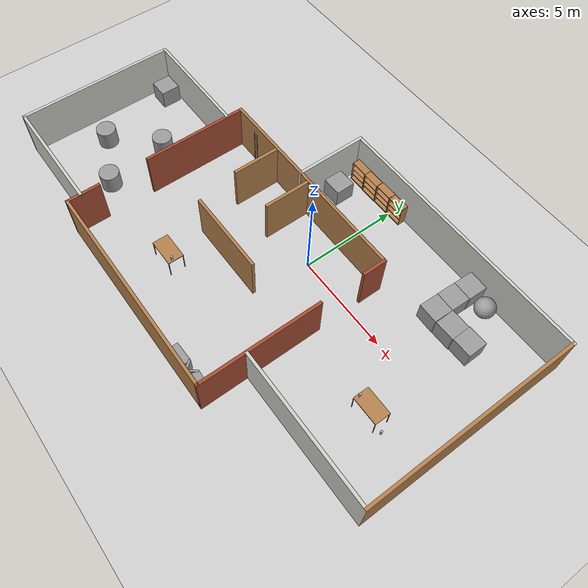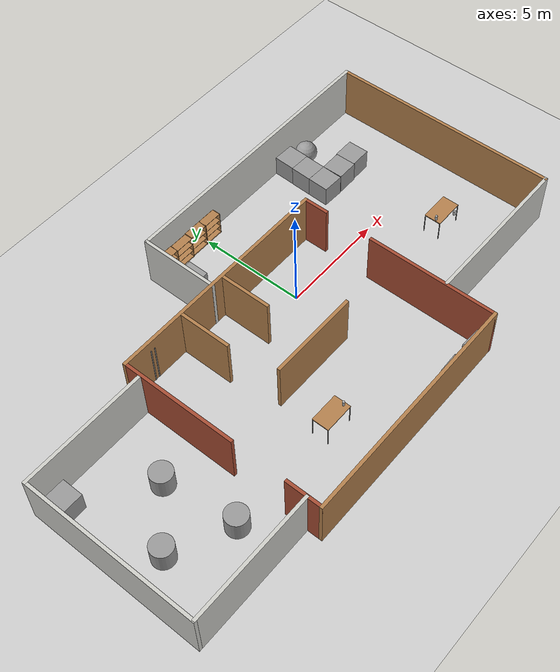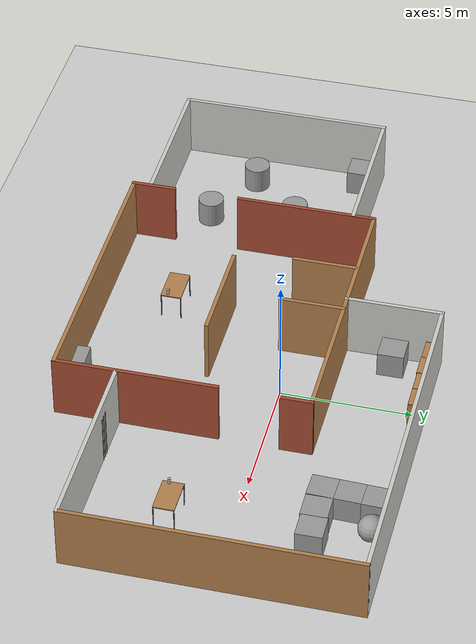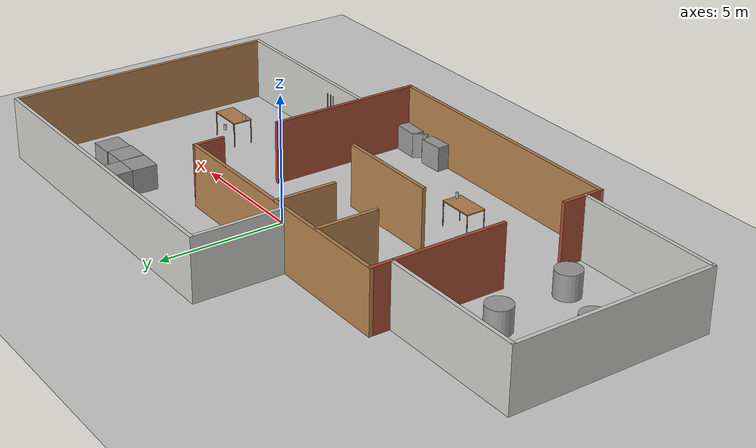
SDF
<sdf version="1.6">
 <world name="default">
  <light name="sun" type="directional">
   <pose>0 0 10 0 -0 0</pose>
   <diffuse>0.8 0.8 0.8 1</diffuse>
   <specular>0.1 0.1 0.1 1</specular>
   <attenuation>
    <range>1000</range>
    <constant>0.9</constant>
    <linear>0.01</linear>
    <quadratic>0.001</quadratic>
   </attenuation>
   <direction>-0.5 0.5 -1</direction>
  </light>
  <model name="ground_plane">
   <static>1</static>
   <link name="link">
    <collision name="collision">
     <geometry><plane><normal>0 0 1</normal><size>100 100</size></plane></geometry>
     <surface><friction><ode><mu>100</mu><mu2>50</mu2></ode></friction></surface>
    </collision>
    <visual name="visual">
     <cast_shadows>0</cast_shadows>
     <geometry><plane><normal>0 0 1</normal><size>100 100</size></plane></geometry>
     <material>
      <script><uri>file://media/materials/scripts/gazebo.material</uri><name>Gazebo/Grey</name></script>
     </material>
    </visual>
   </link>
  </model>
  <gravity>0 0 -9.8</gravity>
  <magnetic_field>6e-06 2.3e-05 -4.2e-05</magnetic_field>
  <atmosphere type="adiabatic"/>
  <physics name="default_physics" default="0" type="ode">
   <max_step_size>0.001</max_step_size>
   <real_time_factor>1</real_time_factor>
   <real_time_update_rate>1000</real_time_update_rate>
  </physics>
  <scene><ambient>0.4 0.4 0.4 1</ambient><background>0.7 0.7 0.7 1</background><shadows>1</shadows></scene>
  <spherical_coordinates>
   <surface_model>EARTH_WGS84</surface_model>
   <latitude_deg>0</latitude_deg>
   <longitude_deg>0</longitude_deg>
   <elevation>0</elevation>
   <heading_deg>0</heading_deg>
  </spherical_coordinates>
  <model name="test_world">
   <pose>-1.78434 -1.17966 0 0 -0 0</pose>
   <link name="Wall_1">
    <collision name="Wall_1_Collision">
     <geometry><box><size>4.25 0.15 2.5</size></box></geometry>
     <pose>0 0 1.25 0 -0 0</pose>
    </collision>
    <visual name="Wall_1_Visual">
     <pose>0 0 1.25 0 -0 0</pose>
     <geometry><box><size>4.25 0.15 2.5</size></box></geometry>
     <material>
      <script><uri>file://media/materials/scripts/gazebo.material</uri><name>Gazebo/Wood</name></script>
      <ambient>1 1 1 1</ambient>
     </material>
    </visual>
    <pose>-0.615659 -1.70034 0 0 -0 3.14159</pose>
   </link>
   <link name="Wall_12">
    <collision name="Wall_12_Collision">
     <geometry><box><size>11 0.15 2.5</size></box></geometry>
     <pose>0 0 1.25 0 -0 0</pose>
    </collision>
    <visual name="Wall_12_Visual">
     <pose>0 0 1.25 0 -0 0</pose>
     <geometry><box><size>11 0.15 2.5</size></box></geometry>
     <material>
      <script><uri>file://media/materials/scripts/gazebo.material</uri><name>Gazebo/Wood</name></script>
      <ambient>1 1 1 1</ambient>
     </material>
    </visual>
    <pose>-0.768184 -6.59875 0 0 -0 0</pose>
   </link>
   <link name="Wall_15">
    <collision name="Wall_15_Collision">
     <geometry><box><size>11 0.15 2.5</size></box></geometry>
     <pose>0 0 1.25 0 -0 0</pose>
    </collision>
    <visual name="Wall_15_Visual">
     <pose>0 0 1.25 0 -0 0</pose>
     <geometry><box><size>11 0.15 2.5</size></box></geometry>
     <material>
      <script><uri>file://media/materials/scripts/gazebo.material</uri><name>Gazebo/Wood</name></script>
      <ambient>1 1 1 1</ambient>
     </material>
    </visual>
    <pose>-0.768184 3.00125 0 0 -0 0</pose>
   </link>
   <link name="Wall_19">
    <collision name="Wall_19_Collision">
     <geometry><box><size>1.25 0.15 2.5</size></box></geometry>
     <pose>0 0 1.25 0 -0 0</pose>
    </collision>
    <visual name="Wall_19_Visual">
     <pose>0 0 1.25 0 -0 0</pose>
     <geometry><box><size>1.25 0.15 2.5</size></box></geometry>
     <material>
      <script><uri>file://media/materials/scripts/gazebo.material</uri><name>Gazebo/Bricks</name></script>
      <ambient>1 1 1 1</ambient>
     </material>
    </visual>
    <pose>4.65682 2.45125 0 0 0 -1.5708</pose>
   </link>
   <link name="Wall_21">
    <collision name="Wall_21_Collision">
     <geometry><box><size>6.25 0.15 2.5</size></box></geometry>
     <pose>0 0 1.25 0 -0 0</pose>
    </collision>
    <visual name="Wall_21_Visual">
     <pose>0 0 1.25 0 -0 0</pose>
     <geometry><box><size>6.25 0.15 2.5</size></box></geometry>
     <material>
      <script><uri>file://media/materials/scripts/gazebo.material</uri><name>Gazebo/Bricks</name></script>
      <ambient>1 1 1 1</ambient>
     </material>
    </visual>
    <pose>4.65682 -3.54875 0 0 -0 1.5708</pose>
   </link>
   <link name="Wall_23">
    <collision name="Wall_23_Collision">
     <geometry><box><size>5.5 0.15 2.5</size></box></geometry>
     <pose>0 0 1.25 0 -0 0</pose>
    </collision>
    <visual name="Wall_23_Visual">
     <pose>0 0 1.25 0 -0 0</pose>
     <geometry><box><size>5.5 0.15 2.5</size></box></geometry>
     <material>
      <script><uri>file://media/materials/scripts/gazebo.material</uri><name>Gazebo/Bricks</name></script>
      <ambient>1 1 1 1</ambient>
     </material>
    </visual>
    <pose>-6.19318 0.326247 0 0 0 -1.5708</pose>
   </link>
   <link name="Wall_25">
    <collision name="Wall_25_Collision">
     <geometry><box><size>1.75 0.15 2.5</size></box></geometry>
     <pose>0 0 1.25 0 -0 0</pose>
    </collision>
    <visual name="Wall_25_Visual">
     <pose>0 0 1.25 0 -0 0</pose>
     <geometry><box><size>1.75 0.15 2.5</size></box></geometry>
     <material>
      <script><uri>file://media/materials/scripts/gazebo.material</uri><name>Gazebo/Bricks</name></script>
      <ambient>1 1 1 1</ambient>
     </material>
    </visual>
    <pose>-6.19318 -5.79875 0 0 -0 1.5708</pose>
   </link>
   <link name="Wall_30">
    <collision name="Wall_30_Collision">
     <geometry><box><size>6 0.15 2.5</size></box></geometry>
     <pose>0 0 1.25 0 -0 0</pose>
    </collision>
    <visual name="Wall_30_Visual">
     <pose>0 0 1.25 0 -0 0</pose>
     <geometry><box><size>6 0.15 2.5</size></box></geometry>
     <material>
      <script><uri>file://media/materials/scripts/gazebo.material</uri><name>Gazebo/CeilingTiled</name></script>
      <ambient>1 1 1 1</ambient>
     </material>
    </visual>
    <pose>-9.15006 2.17634 0 0 -0 3.14159</pose>
   </link>
   <link name="Wall_31">
    <collision name="Wall_31_Collision">
     <geometry><box><size>8.25 0.15 2.5</size></box></geometry>
     <pose>0 0 1.25 0 -0 0</pose>
    </collision>
    <visual name="Wall_31_Visual">
     <pose>0 0 1.25 0 -0 0</pose>
     <geometry><box><size>8.25 0.15 2.5</size></box></geometry>
     <material>
      <script><uri>file://media/materials/scripts/gazebo.material</uri><name>Gazebo/CeilingTiled</name></script>
      <ambient>0.435294 0.796078 0.67451 1</ambient>
     </material>
    </visual>
    <pose>-12.0751 -1.87366 0 0 0 -1.5708</pose>
   </link>
   <link name="Wall_32">
    <collision name="Wall_32_Collision">
     <geometry><box><size>6 0.15 2.5</size></box></geometry>
     <pose>0 0 1.25 0 -0 0</pose>
    </collision>
    <visual name="Wall_32_Visual">
     <pose>0 0 1.25 0 -0 0</pose>
     <geometry><box><size>6 0.15 2.5</size></box></geometry>
     <material>
      <script><uri>file://media/materials/scripts/gazebo.material</uri><name>Gazebo/CeilingTiled</name></script>
      <ambient>1 1 1 1</ambient>
     </material>
    </visual>
    <pose>-9.15006 -5.92366 0 0 -0 0</pose>
   </link>
   <link name="Wall_34">
    <collision name="Wall_34_Collision">
     <geometry><box><size>2.5 0.15 2.5</size></box></geometry>
     <pose>0 0 1.25 0 -0 0</pose>
    </collision>
    <visual name="Wall_34_Visual">
     <pose>0 0 1.25 0 -0 0</pose>
     <geometry><box><size>2.5 0.15 2.5</size></box></geometry>
     <material>
      <script><uri>file://media/materials/scripts/gazebo.material</uri><name>Gazebo/Wood</name></script>
      <ambient>1 1 1 1</ambient>
     </material>
    </visual>
    <pose>-3.10226 1.75436 0 0 0 -1.5708</pose>
   </link>
   <link name="Wall_37">
    <collision name="Wall_37_Collision">
     <geometry><box><size>2.5 0.15 2.5</size></box></geometry>
     <pose>0 0 1.25 0 -0 0</pose>
    </collision>
    <visual name="Wall_37_Visual">
     <pose>0 0 1.25 0 -0 0</pose>
     <geometry><box><size>2.5 0.15 2.5</size></box></geometry>
     <material>
      <script><uri>file://media/materials/scripts/gazebo.material</uri><name>Gazebo/Wood</name></script>
      <ambient>1 1 1 1</ambient>
     </material>
    </visual>
    <pose>-0.673547 1.80062 0 0 0 -1.5708</pose>
   </link>
   <link name="Wall_39">
    <collision name="Wall_39_Collision">
     <geometry><box><size>3.75 0.15 2.5</size></box></geometry>
     <pose>0 0 1.25 0 -0 0</pose>
    </collision>
    <visual name="Wall_39_Visual">
     <pose>0 0 1.25 0 -0 0</pose>
     <geometry><box><size>3.75 0.15 2.5</size></box></geometry>
     <material>
      <script><uri>file://media/materials/scripts/gazebo.material</uri><name>Gazebo/CeilingTiled</name></script>
      <ambient>1 1 1 1</ambient>
     </material>
    </visual>
    <pose>-1.27494 4.79875 0 0 -0 1.5708</pose>
   </link>
   <link name="Wall_40">
    <collision name="Wall_40_Collision">
     <geometry><box><size>13.5 0.15 2.5</size></box></geometry>
     <pose>0 0 1.25 0 -0 0</pose>
    </collision>
    <visual name="Wall_40_Visual">
     <pose>0 0 1.25 0 -0 0</pose>
     <geometry><box><size>13.5 0.15 2.5</size></box></geometry>
     <material>
      <script><uri>file://media/materials/scripts/gazebo.material</uri><name>Gazebo/CeilingTiled</name></script>
      <ambient>1 1 1 1</ambient>
     </material>
    </visual>
    <pose>5.40006 6.59875 0 0 -0 0</pose>
   </link>
   <link name="Wall_41">
    <collision name="Wall_41_Collision">
     <geometry><box><size>11 0.15 2.5</size></box></geometry>
     <pose>0 0 1.25 0 -0 0</pose>
    </collision>
    <visual name="Wall_41_Visual">
     <pose>0 0 1.25 0 -0 0</pose>
     <geometry><box><size>11 0.15 2.5</size></box></geometry>
     <material>
      <script><uri>file://media/materials/scripts/gazebo.material</uri><name>Gazebo/Wood</name></script>
      <ambient>1 1 1 1</ambient>
     </material>
    </visual>
    <pose>12.0751 1.17375 0 0 0 -1.5708</pose>
   </link>
   <link name="Wall_42">
    <collision name="Wall_42_Collision">
     <geometry><box><size>7.5 0.15 2.5</size></box></geometry>
     <pose>0 0 1.25 0 -0 0</pose>
    </collision>
    <visual name="Wall_42_Visual">
     <pose>0 0 1.25 0 -0 0</pose>
     <geometry><box><size>7.5 0.15 2.5</size></box></geometry>
     <material>
      <script><uri>file://media/materials/scripts/gazebo.material</uri><name>Gazebo/CeilingTiled</name></script>
      <ambient>1 1 1 1</ambient>
     </material>
    </visual>
    <pose>8.40006 -4.25125 0 0 -0 3.14159</pose>
   </link>
   <static>1</static>
  </model>
  <model name="table">
   <static>0</static>
   <link name="link">
    <collision name="surface">
     <pose>0 0 1 0 -0 0</pose>
     <geometry><box><size>1.5 0.8 0.03</size></box></geometry>
     <surface><friction><ode><mu>0.6</mu><mu2>0.6</mu2></ode></friction></surface>
    </collision>
    <visual name="visual1">
     <pose>0 0 1 0 -0 0</pose>
     <geometry><box><size>1.4 0.8 0.04</size></box></geometry>
     <material>
      <script><uri>file://media/materials/scripts/gazebo.material</uri><name>Gazebo/Wood</name></script>
     </material>
    </visual>
    <collision name="front_left_leg">
     <pose>0.68 0.38 0.5 0 -0 0</pose>
     <geometry><cylinder><radius>0.02</radius><length>1</length></cylinder></geometry>
    </collision>
    <visual name="front_left_leg">
     <pose>0.68 0.38 0.5 0 -0 0</pose>
     <geometry><cylinder><radius>0.02</radius><length>1</length></cylinder></geometry>
     <material>
      <script><uri>file://media/materials/scripts/gazebo.material</uri><name>Gazebo/Grey</name></script>
     </material>
    </visual>
    <collision name="front_right_leg">
     <pose>0.68 -0.38 0.5 0 -0 0</pose>
     <geometry><cylinder><radius>0.02</radius><length>1</length></cylinder></geometry>
    </collision>
    <visual name="front_right_leg">
     <pose>0.68 -0.38 0.5 0 -0 0</pose>
     <geometry><cylinder><radius>0.02</radius><length>1</length></cylinder></geometry>
     <material>
      <script><uri>file://media/materials/scripts/gazebo.material</uri><name>Gazebo/Grey</name></script>
     </material>
    </visual>
    <collision name="back_right_leg">
     <pose>-0.68 -0.38 0.5 0 -0 0</pose>
     <geometry><cylinder><radius>0.02</radius><length>1</length></cylinder></geometry>
    </collision>
    <visual name="back_right_leg">
     <pose>-0.68 -0.38 0.5 0 -0 0</pose>
     <geometry><cylinder><radius>0.02</radius><length>1</length></cylinder></geometry>
     <material>
      <script><uri>file://media/materials/scripts/gazebo.material</uri><name>Gazebo/Grey</name></script>
     </material>
    </visual>
    <collision name="back_left_leg">
     <pose>-0.68 0.38 0.5 0 -0 0</pose>
     <geometry><cylinder><radius>0.02</radius><length>1</length></cylinder></geometry>
    </collision>
    <visual name="back_left_leg">
     <pose>-0.68 0.38 0.5 0 -0 0</pose>
     <geometry><cylinder><radius>0.02</radius><length>1</length></cylinder></geometry>
     <material>
      <script><uri>file://media/materials/scripts/gazebo.material</uri><name>Gazebo/Grey</name></script>
     </material>
    </visual>
    <inertial>
     <inertia><ixx>1</ixx><ixy>0</ixy><ixz>0</ixz><iyy>1</iyy><iyz>0</iyz><izz>1</izz></inertia>
     <mass>1</mass>
    </inertial>
   </link>
   <pose>-4.01579 -5.0682 -0.019985 0.00133 0.005489 -0.000608</pose>
  </model>
  <model name="unit_box_0_2">
   <pose>5.46329 2.82899 0.499995 -1e-05 -0 -0.031279</pose>
   <link name="link">
    <inertial>
     <mass>1</mass>
     <inertia>
      <ixx>0.166667</ixx>
      <ixy>0</ixy>
      <ixz>0</ixz>
      <iyy>0.166667</iyy>
      <iyz>0</iyz>
      <izz>0.166667</izz>
     </inertia>
    </inertial>
    <collision name="collision"><geometry><box><size>1 1 1</size></box></geometry></collision>
    <visual name="visual">
     <geometry><box><size>1 1 1</size></box></geometry>
     <material>
      <script><name>Gazebo/Grey</name><uri>file://media/materials/scripts/gazebo.material</uri></script>
     </material>
    </visual>
   </link>
  </model>
  <model name="unit_box_0_3">
   <pose>5.53381 4.82824 0.499995 -1e-05 0 -0.032223</pose>
   <link name="link">
    <inertial>
     <mass>1</mass>
     <inertia>
      <ixx>0.166667</ixx>
      <ixy>0</ixy>
      <ixz>0</ixz>
      <iyy>0.166667</iyy>
      <iyz>0</iyz>
      <izz>0.166667</izz>
     </inertia>
    </inertial>
    <collision name="collision"><geometry><box><size>1 1 1</size></box></geometry></collision>
    <visual name="visual">
     <geometry><box><size>1 1 1</size></box></geometry>
     <material>
      <script><name>Gazebo/Grey</name><uri>file://media/materials/scripts/gazebo.material</uri></script>
     </material>
    </visual>
   </link>
  </model>
  <model name="unit_box_0_4">
   <pose>5.49328 3.82901 0.499995 1e-05 -0 -0.032214</pose>
   <link name="link">
    <inertial>
     <mass>1</mass>
     <inertia>
      <ixx>0.166667</ixx>
      <ixy>0</ixy>
      <ixz>0</ixz>
      <iyy>0.166667</iyy>
      <iyz>0</iyz>
      <izz>0.166667</izz>
     </inertia>
    </inertial>
    <collision name="collision"><geometry><box><size>1 1 1</size></box></geometry></collision>
    <visual name="visual">
     <geometry><box><size>1 1 1</size></box></geometry>
     <material>
      <script><name>Gazebo/Grey</name><uri>file://media/materials/scripts/gazebo.material</uri></script>
     </material>
    </visual>
   </link>
  </model>
  <model name="unit_box_0_5">
   <pose>6.48296 2.82872 0.5 0 -0 0.008783</pose>
   <link name="link">
    <inertial>
     <mass>1</mass>
     <inertia>
      <ixx>0.166667</ixx>
      <ixy>0</ixy>
      <ixz>0</ixz>
      <iyy>0.166667</iyy>
      <iyz>0</iyz>
      <izz>0.166667</izz>
     </inertia>
    </inertial>
    <collision name="collision"><geometry><box><size>1 1 1</size></box></geometry></collision>
    <visual name="visual">
     <geometry><box><size>1 1 1</size></box></geometry>
     <material>
      <script><name>Gazebo/Grey</name><uri>file://media/materials/scripts/gazebo.material</uri></script>
     </material>
    </visual>
   </link>
  </model>
  <model name="unit_box_0_6">
   <pose>7.48259 2.8746 0.494019 0.001468 0.000371 0.008756</pose>
   <link name="link">
    <inertial>
     <mass>1</mass>
     <inertia>
      <ixx>0.166667</ixx>
      <ixy>0</ixy>
      <ixz>0</ixz>
      <iyy>0.166667</iyy>
      <iyz>0</iyz>
      <izz>0.166667</izz>
     </inertia>
    </inertial>
    <collision name="collision"><geometry><box><size>1 1 1</size></box></geometry></collision>
    <visual name="visual">
     <geometry><box><size>1 1 1</size></box></geometry>
     <material>
      <script><name>Gazebo/Grey</name><uri>file://media/materials/scripts/gazebo.material</uri></script>
     </material>
    </visual>
   </link>
  </model>
  <model name="bookshelf_1">
   <static>1</static>
   <link name="link">
    <inertial><mass>1</mass></inertial>
    <collision name="back">
     <pose>0 0.005 0.6 0 -0 0</pose>
     <geometry><box><size>0.9 0.01 1.2</size></box></geometry>
    </collision>
    <visual name="visual1">
     <pose>0 0.005 0.6 0 -0 0</pose>
     <geometry><box><size>0.9 0.01 1.2</size></box></geometry>
     <material>
      <script><uri>file://media/materials/scripts/gazebo.material</uri><name>Gazebo/Wood</name></script>
     </material>
    </visual>
    <collision name="left_side">
     <pose>0.45 -0.195 0.6 0 -0 0</pose>
     <geometry><box><size>0.02 0.4 1.2</size></box></geometry>
    </collision>
    <visual name="visual2">
     <pose>0.45 -0.195 0.6 0 -0 0</pose>
     <geometry><box><size>0.02 0.4 1.2</size></box></geometry>
     <material>
      <script><uri>file://media/materials/scripts/gazebo.material</uri><name>Gazebo/Wood</name></script>
     </material>
    </visual>
    <collision name="right_side">
     <pose>-0.45 -0.195 0.6 0 -0 0</pose>
     <geometry><box><size>0.02 0.4 1.2</size></box></geometry>
    </collision>
    <visual name="visual3">
     <pose>-0.45 -0.195 0.6 0 -0 0</pose>
     <geometry><box><size>0.02 0.4 1.2</size></box></geometry>
     <material>
      <script><uri>file://media/materials/scripts/gazebo.material</uri><name>Gazebo/Wood</name></script>
     </material>
    </visual>
    <collision name="bottom">
     <pose>0 -0.195 0.03 0 -0 0</pose>
     <geometry><box><size>0.88 0.4 0.06</size></box></geometry>
    </collision>
    <visual name="visual4">
     <pose>0 -0.195 0.03 0 -0 0</pose>
     <geometry><box><size>0.88 0.4 0.06</size></box></geometry>
     <material>
      <script><uri>file://media/materials/scripts/gazebo.material</uri><name>Gazebo/Wood</name></script>
     </material>
    </visual>
    <collision name="top">
     <pose>0 -0.195 1.19 0 -0 0</pose>
     <geometry><box><size>0.88 0.4 0.02</size></box></geometry>
    </collision>
    <visual name="visual5">
     <pose>0 -0.195 1.19 0 -0 0</pose>
     <geometry><box><size>0.88 0.4 0.02</size></box></geometry>
     <material>
      <script><uri>file://media/materials/scripts/gazebo.material</uri><name>Gazebo/Wood</name></script>
     </material>
    </visual>
    <collision name="low_shelf">
     <pose>0 -0.195 0.43 0 -0 0</pose>
     <geometry><box><size>0.88 0.4 0.02</size></box></geometry>
    </collision>
    <visual name="visual6">
     <pose>0 -0.195 0.43 0 -0 0</pose>
     <geometry><box><size>0.88 0.4 0.02</size></box></geometry>
     <material>
      <script><uri>file://media/materials/scripts/gazebo.material</uri><name>Gazebo/Wood</name></script>
     </material>
    </visual>
    <collision name="high_shelf">
     <pose>0 -0.195 0.8 0 -0 0</pose>
     <geometry><box><size>0.88 0.4 0.02</size></box></geometry>
    </collision>
    <visual name="visual7">
     <pose>0 -0.195 0.8 0 -0 0</pose>
     <geometry><box><size>0.88 0.4 0.02</size></box></geometry>
     <material>
      <script><uri>file://media/materials/scripts/gazebo.material</uri><name>Gazebo/Wood</name></script>
     </material>
    </visual>
   </link>
   <pose>-2.35602 5.3174 0 0 -0 0</pose>
  </model>
  <model name="bookshelf_1_clone">
   <static>1</static>
   <link name="link">
    <inertial><mass>1</mass></inertial>
    <collision name="back">
     <pose>0 0.005 0.6 0 -0 0</pose>
     <geometry><box><size>0.9 0.01 1.2</size></box></geometry>
    </collision>
    <visual name="visual1">
     <pose>0 0.005 0.6 0 -0 0</pose>
     <geometry><box><size>0.9 0.01 1.2</size></box></geometry>
     <material>
      <script><uri>file://media/materials/scripts/gazebo.material</uri><name>Gazebo/Wood</name></script>
     </material>
    </visual>
    <collision name="left_side">
     <pose>0.45 -0.195 0.6 0 -0 0</pose>
     <geometry><box><size>0.02 0.4 1.2</size></box></geometry>
    </collision>
    <visual name="visual2">
     <pose>0.45 -0.195 0.6 0 -0 0</pose>
     <geometry><box><size>0.02 0.4 1.2</size></box></geometry>
     <material>
      <script><uri>file://media/materials/scripts/gazebo.material</uri><name>Gazebo/Wood</name></script>
     </material>
    </visual>
    <collision name="right_side">
     <pose>-0.45 -0.195 0.6 0 -0 0</pose>
     <geometry><box><size>0.02 0.4 1.2</size></box></geometry>
    </collision>
    <visual name="visual3">
     <pose>-0.45 -0.195 0.6 0 -0 0</pose>
     <geometry><box><size>0.02 0.4 1.2</size></box></geometry>
     <material>
      <script><uri>file://media/materials/scripts/gazebo.material</uri><name>Gazebo/Wood</name></script>
     </material>
    </visual>
    <collision name="bottom">
     <pose>0 -0.195 0.03 0 -0 0</pose>
     <geometry><box><size>0.88 0.4 0.06</size></box></geometry>
    </collision>
    <visual name="visual4">
     <pose>0 -0.195 0.03 0 -0 0</pose>
     <geometry><box><size>0.88 0.4 0.06</size></box></geometry>
     <material>
      <script><uri>file://media/materials/scripts/gazebo.material</uri><name>Gazebo/Wood</name></script>
     </material>
    </visual>
    <collision name="top">
     <pose>0 -0.195 1.19 0 -0 0</pose>
     <geometry><box><size>0.88 0.4 0.02</size></box></geometry>
    </collision>
    <visual name="visual5">
     <pose>0 -0.195 1.19 0 -0 0</pose>
     <geometry><box><size>0.88 0.4 0.02</size></box></geometry>
     <material>
      <script><uri>file://media/materials/scripts/gazebo.material</uri><name>Gazebo/Wood</name></script>
     </material>
    </visual>
    <collision name="low_shelf">
     <pose>0 -0.195 0.43 0 -0 0</pose>
     <geometry><box><size>0.88 0.4 0.02</size></box></geometry>
    </collision>
    <visual name="visual6">
     <pose>0 -0.195 0.43 0 -0 0</pose>
     <geometry><box><size>0.88 0.4 0.02</size></box></geometry>
     <material>
      <script><uri>file://media/materials/scripts/gazebo.material</uri><name>Gazebo/Wood</name></script>
     </material>
    </visual>
    <collision name="high_shelf">
     <pose>0 -0.195 0.8 0 -0 0</pose>
     <geometry><box><size>0.88 0.4 0.02</size></box></geometry>
    </collision>
    <visual name="visual7">
     <pose>0 -0.195 0.8 0 -0 0</pose>
     <geometry><box><size>0.88 0.4 0.02</size></box></geometry>
     <material>
      <script><uri>file://media/materials/scripts/gazebo.material</uri><name>Gazebo/Wood</name></script>
     </material>
    </visual>
   </link>
   <pose>-1.47476 5.29885 0 0 -0 0</pose>
  </model>
  <model name="bookshelf_1_clone_0">
   <static>1</static>
   <link name="link">
    <inertial><mass>1</mass></inertial>
    <collision name="back">
     <pose>0 0.005 0.6 0 -0 0</pose>
     <geometry><box><size>0.9 0.01 1.2</size></box></geometry>
    </collision>
    <visual name="visual1">
     <pose>0 0.005 0.6 0 -0 0</pose>
     <geometry><box><size>0.9 0.01 1.2</size></box></geometry>
     <material>
      <script><uri>file://media/materials/scripts/gazebo.material</uri><name>Gazebo/Wood</name></script>
     </material>
    </visual>
    <collision name="left_side">
     <pose>0.45 -0.195 0.6 0 -0 0</pose>
     <geometry><box><size>0.02 0.4 1.2</size></box></geometry>
    </collision>
    <visual name="visual2">
     <pose>0.45 -0.195 0.6 0 -0 0</pose>
     <geometry><box><size>0.02 0.4 1.2</size></box></geometry>
     <material>
      <script><uri>file://media/materials/scripts/gazebo.material</uri><name>Gazebo/Wood</name></script>
     </material>
    </visual>
    <collision name="right_side">
     <pose>-0.45 -0.195 0.6 0 -0 0</pose>
     <geometry><box><size>0.02 0.4 1.2</size></box></geometry>
    </collision>
    <visual name="visual3">
     <pose>-0.45 -0.195 0.6 0 -0 0</pose>
     <geometry><box><size>0.02 0.4 1.2</size></box></geometry>
     <material>
      <script><uri>file://media/materials/scripts/gazebo.material</uri><name>Gazebo/Wood</name></script>
     </material>
    </visual>
    <collision name="bottom">
     <pose>0 -0.195 0.03 0 -0 0</pose>
     <geometry><box><size>0.88 0.4 0.06</size></box></geometry>
    </collision>
    <visual name="visual4">
     <pose>0 -0.195 0.03 0 -0 0</pose>
     <geometry><box><size>0.88 0.4 0.06</size></box></geometry>
     <material>
      <script><uri>file://media/materials/scripts/gazebo.material</uri><name>Gazebo/Wood</name></script>
     </material>
    </visual>
    <collision name="top">
     <pose>0 -0.195 1.19 0 -0 0</pose>
     <geometry><box><size>0.88 0.4 0.02</size></box></geometry>
    </collision>
    <visual name="visual5">
     <pose>0 -0.195 1.19 0 -0 0</pose>
     <geometry><box><size>0.88 0.4 0.02</size></box></geometry>
     <material>
      <script><uri>file://media/materials/scripts/gazebo.material</uri><name>Gazebo/Wood</name></script>
     </material>
    </visual>
    <collision name="low_shelf">
     <pose>0 -0.195 0.43 0 -0 0</pose>
     <geometry><box><size>0.88 0.4 0.02</size></box></geometry>
    </collision>
    <visual name="visual6">
     <pose>0 -0.195 0.43 0 -0 0</pose>
     <geometry><box><size>0.88 0.4 0.02</size></box></geometry>
     <material>
      <script><uri>file://media/materials/scripts/gazebo.material</uri><name>Gazebo/Wood</name></script>
     </material>
    </visual>
    <collision name="high_shelf">
     <pose>0 -0.195 0.8 0 -0 0</pose>
     <geometry><box><size>0.88 0.4 0.02</size></box></geometry>
    </collision>
    <visual name="visual7">
     <pose>0 -0.195 0.8 0 -0 0</pose>
     <geometry><box><size>0.88 0.4 0.02</size></box></geometry>
     <material>
      <script><uri>file://media/materials/scripts/gazebo.material</uri><name>Gazebo/Wood</name></script>
     </material>
    </visual>
   </link>
   <pose>-0.562909 5.32299 0 0 -0 0</pose>
  </model>
  <model name="bookshelf_1_clone_1">
   <static>1</static>
   <link name="link">
    <inertial><mass>1</mass></inertial>
    <collision name="back">
     <pose>0 0.005 0.6 0 -0 0</pose>
     <geometry><box><size>0.9 0.01 1.2</size></box></geometry>
    </collision>
    <visual name="visual1">
     <pose>0 0.005 0.6 0 -0 0</pose>
     <geometry><box><size>0.9 0.01 1.2</size></box></geometry>
     <material>
      <script><uri>file://media/materials/scripts/gazebo.material</uri><name>Gazebo/Wood</name></script>
     </material>
    </visual>
    <collision name="left_side">
     <pose>0.45 -0.195 0.6 0 -0 0</pose>
     <geometry><box><size>0.02 0.4 1.2</size></box></geometry>
    </collision>
    <visual name="visual2">
     <pose>0.45 -0.195 0.6 0 -0 0</pose>
     <geometry><box><size>0.02 0.4 1.2</size></box></geometry>
     <material>
      <script><uri>file://media/materials/scripts/gazebo.material</uri><name>Gazebo/Wood</name></script>
     </material>
    </visual>
    <collision name="right_side">
     <pose>-0.45 -0.195 0.6 0 -0 0</pose>
     <geometry><box><size>0.02 0.4 1.2</size></box></geometry>
    </collision>
    <visual name="visual3">
     <pose>-0.45 -0.195 0.6 0 -0 0</pose>
     <geometry><box><size>0.02 0.4 1.2</size></box></geometry>
     <material>
      <script><uri>file://media/materials/scripts/gazebo.material</uri><name>Gazebo/Wood</name></script>
     </material>
    </visual>
    <collision name="bottom">
     <pose>0 -0.195 0.03 0 -0 0</pose>
     <geometry><box><size>0.88 0.4 0.06</size></box></geometry>
    </collision>
    <visual name="visual4">
     <pose>0 -0.195 0.03 0 -0 0</pose>
     <geometry><box><size>0.88 0.4 0.06</size></box></geometry>
     <material>
      <script><uri>file://media/materials/scripts/gazebo.material</uri><name>Gazebo/Wood</name></script>
     </material>
    </visual>
    <collision name="top">
     <pose>0 -0.195 1.19 0 -0 0</pose>
     <geometry><box><size>0.88 0.4 0.02</size></box></geometry>
    </collision>
    <visual name="visual5">
     <pose>0 -0.195 1.19 0 -0 0</pose>
     <geometry><box><size>0.88 0.4 0.02</size></box></geometry>
     <material>
      <script><uri>file://media/materials/scripts/gazebo.material</uri><name>Gazebo/Wood</name></script>
     </material>
    </visual>
    <collision name="low_shelf">
     <pose>0 -0.195 0.43 0 -0 0</pose>
     <geometry><box><size>0.88 0.4 0.02</size></box></geometry>
    </collision>
    <visual name="visual6">
     <pose>0 -0.195 0.43 0 -0 0</pose>
     <geometry><box><size>0.88 0.4 0.02</size></box></geometry>
     <material>
      <script><uri>file://media/materials/scripts/gazebo.material</uri><name>Gazebo/Wood</name></script>
     </material>
    </visual>
    <collision name="high_shelf">
     <pose>0 -0.195 0.8 0 -0 0</pose>
     <geometry><box><size>0.88 0.4 0.02</size></box></geometry>
    </collision>
    <visual name="visual7">
     <pose>0 -0.195 0.8 0 -0 0</pose>
     <geometry><box><size>0.88 0.4 0.02</size></box></geometry>
     <material>
      <script><uri>file://media/materials/scripts/gazebo.material</uri><name>Gazebo/Wood</name></script>
     </material>
    </visual>
   </link>
   <pose>0.313567 5.32284 0 0 -0 0</pose>
  </model>
  <model name="beer">
   <link name="link">
    <pose>0 0 0.115 0 -0 0</pose>
    <inertial>
     <mass>0.39</mass>
     <inertia><ixx>0.00058</ixx><ixy>0</ixy><ixz>0</ixz><iyy>0.00058</iyy><iyz>0</iyz><izz>0.00019</izz></inertia>
    </inertial>
    <collision name="collision">
     <geometry><cylinder><radius>0.055</radius><length>0.23</length></cylinder></geometry>
    </collision>
    <visual name="visual">
     <geometry><cylinder><radius>0.055</radius><length>0.23</length></cylinder></geometry>
     <material>
      <script>
       <uri>model://beer/materials/scripts</uri>
       <uri>model://beer/materials/textures</uri>
       <name>Beer/Diffuse</name>
      </script>
     </material>
    </visual>
   </link>
   <pose>-3.44186 -5.20673 0.991693 0.004765 0.003571 0.688015</pose>
  </model>
  <model name="beer_clone_1">
   <link name="link">
    <pose>0 0 0.115 0 -0 0</pose>
    <inertial>
     <mass>0.39</mass>
     <inertia><ixx>0.00058</ixx><ixy>0</ixy><ixz>0</ixz><iyy>0.00058</iyy><iyz>0</iyz><izz>0.00019</izz></inertia>
    </inertial>
    <collision name="collision">
     <geometry><cylinder><radius>0.055</radius><length>0.23</length></cylinder></geometry>
    </collision>
    <visual name="visual">
     <geometry><cylinder><radius>0.055</radius><length>0.23</length></cylinder></geometry>
     <material>
      <script>
       <uri>model://beer/materials/scripts</uri>
       <uri>model://beer/materials/textures</uri>
       <name>Beer/Diffuse</name>
      </script>
     </material>
    </visual>
   </link>
   <pose>8.10989 -2.46159 0.230065 -3.14054 -0.000581 2.77993</pose>
  </model>
  <model name="beer_clone_2">
   <link name="link">
    <pose>0 0 0.115 0 -0 0</pose>
    <inertial>
     <mass>0.39</mass>
     <inertia><ixx>0.00058</ixx><ixy>0</ixy><ixz>0</ixz><iyy>0.00058</iyy><iyz>0</iyz><izz>0.00019</izz></inertia>
    </inertial>
    <collision name="collision">
     <geometry><cylinder><radius>0.055</radius><length>0.23</length></cylinder></geometry>
    </collision>
    <visual name="visual">
     <geometry><cylinder><radius>0.055</radius><length>0.23</length></cylinder></geometry>
     <material>
      <script>
       <uri>model://beer/materials/scripts</uri>
       <uri>model://beer/materials/textures</uri>
       <name>Beer/Diffuse</name>
      </script>
     </material>
    </visual>
   </link>
   <pose>6.58813 -2.4604 0.990994 -0.005496 -0.003168 1.25338</pose>
  </model>
  <model name="unit_box_0">
   <pose>-13.0086 0.313386 0.5 0 -0 0</pose>
   <link name="link">
    <inertial>
     <mass>1</mass>
     <inertia>
      <ixx>0.166667</ixx>
      <ixy>0</ixy>
      <ixz>0</ixz>
      <iyy>0.166667</iyy>
      <iyz>0</iyz>
      <izz>0.166667</izz>
     </inertia>
    </inertial>
    <collision name="collision"><geometry><box><size>1 1 1</size></box></geometry></collision>
    <visual name="visual">
     <geometry><box><size>1 1 1</size></box></geometry>
     <material>
      <script><name>Gazebo/Grey</name><uri>file://media/materials/scripts/gazebo.material</uri></script>
     </material>
    </visual>
   </link>
  </model>
  <model name="unit_box_2">
   <pose>-2.41052 3.74891 0.5 0 -0 0</pose>
   <link name="link">
    <inertial>
     <mass>1</mass>
     <inertia>
      <ixx>0.166667</ixx>
      <ixy>0</ixy>
      <ixz>0</ixz>
      <iyy>0.166667</iyy>
      <iyz>0</iyz>
      <izz>0.166667</izz>
     </inertia>
    </inertial>
    <collision name="collision"><geometry><box><size>1 1 1</size></box></geometry></collision>
    <visual name="visual">
     <geometry><box><size>1 1 1</size></box></geometry>
     <material>
      <script><name>Gazebo/Grey</name><uri>file://media/materials/scripts/gazebo.material</uri></script>
     </material>
    </visual>
   </link>
  </model>
  <model name="unit_sphere_0">
   <pose>6.60391 4.83797 0.5 0.012288 -0 0</pose>
   <link name="link">
    <inertial>
     <mass>1</mass>
     <inertia><ixx>0.1</ixx><ixy>0</ixy><ixz>0</ixz><iyy>0.1</iyy><iyz>0</iyz><izz>0.1</izz></inertia>
    </inertial>
    <collision name="collision"><geometry><sphere><radius>0.5</radius></sphere></geometry></collision>
    <visual name="visual">
     <geometry><sphere><radius>0.5</radius></sphere></geometry>
     <material>
      <script><name>Gazebo/Grey</name><uri>file://media/materials/scripts/gazebo.material</uri></script>
     </material>
    </visual>
   </link>
  </model>
  <model name="boxDaBox">
   <link name="link">
    <inertial>
     <mass>1</mass>
     <inertia>
      <ixx>0.166667</ixx>
      <ixy>0</ixy>
      <ixz>0</ixz>
      <iyy>0.166667</iyy>
      <iyz>0</iyz>
      <izz>0.166667</izz>
     </inertia>
    </inertial>
    <visual name="visual">
     <geometry><box><size>0.0525 0.01 2</size></box></geometry>
     <material>
      <script><name>Gazebo/Grey</name><uri>file://media/materials/scripts/gazebo.material</uri></script>
      <ambient>0.3 0.3 0.3 1</ambient>
      <diffuse>0.7 0.7 0.7 1</diffuse>
      <specular>0.01 0.01 0.01 1</specular>
      <emissive>0 0 0 1</emissive>
      <shader type="vertex"><normal_map>__default__</normal_map></shader>
     </material>
    </visual>
    <collision name="collision">
     <laser_retro>1</laser_retro>
     <geometry><box><size>0.0525 0.01 2</size></box></geometry>
     <surface>
      <friction>
       <ode><mu>1</mu><mu2>1</mu2><fdir1>0 0 0</fdir1><slip1>0</slip1><slip2>0</slip2></ode>
       <torsional>
        <coefficient>1</coefficient>
        <patch_radius>0</patch_radius>
        <surface_radius>0</surface_radius>
        <use_patch_radius>1</use_patch_radius>
        <ode><slip>0</slip></ode>
       </torsional>
      </friction>
      <bounce><restitution_coefficient>0</restitution_coefficient><threshold>1e+06</threshold></bounce>
      <contact>
       <collide_without_contact>0</collide_without_contact>
       <collide_without_contact_bitmask>1</collide_without_contact_bitmask>
       <collide_bitmask>1</collide_bitmask>
       <ode>
        <soft_cfm>0</soft_cfm>
        <soft_erp>0.2</soft_erp>
        <kp>1e+13</kp>
        <kd>1</kd>
        <max_vel>0.01</max_vel>
        <min_depth>0</min_depth>
       </ode>
       <bullet>
        <split_impulse>1</split_impulse>
        <split_impulse_penetration_threshold>-0.01</split_impulse_penetration_threshold>
        <soft_cfm>0</soft_cfm>
        <soft_erp>0.2</soft_erp>
        <kp>1e+13</kp>
        <kd>1</kd>
       </bullet>
      </contact>
     </surface>
    </collision>
   </link>
   <static>0</static>
   <pose>-6.52165 1.73709 1 -5e-06 2e-06 0.000301</pose>
  </model>
  <model name="boxDaBox_0">
   <link name="link">
    <inertial>
     <mass>1</mass>
     <inertia>
      <ixx>0.166667</ixx>
      <ixy>0</ixy>
      <ixz>0</ixz>
      <iyy>0.166667</iyy>
      <iyz>0</iyz>
      <izz>0.166667</izz>
     </inertia>
    </inertial>
    <visual name="visual">
     <geometry><box><size>0.0525 0.01 2</size></box></geometry>
     <material>
      <script><name>Gazebo/Grey</name><uri>file://media/materials/scripts/gazebo.material</uri></script>
      <ambient>0.3 0.3 0.3 1</ambient>
      <diffuse>0.7 0.7 0.7 1</diffuse>
      <specular>0.01 0.01 0.01 1</specular>
      <emissive>0 0 0 1</emissive>
      <shader type="vertex"><normal_map>__default__</normal_map></shader>
     </material>
    </visual>
    <collision name="collision">
     <laser_retro>1</laser_retro>
     <geometry><box><size>0.0525 0.01 2</size></box></geometry>
     <surface>
      <friction>
       <ode><mu>1</mu><mu2>1</mu2><fdir1>0 0 0</fdir1><slip1>0</slip1><slip2>0</slip2></ode>
       <torsional>
        <coefficient>1</coefficient>
        <patch_radius>0</patch_radius>
        <surface_radius>0</surface_radius>
        <use_patch_radius>1</use_patch_radius>
        <ode><slip>0</slip></ode>
       </torsional>
      </friction>
      <bounce><restitution_coefficient>0</restitution_coefficient><threshold>1e+06</threshold></bounce>
      <contact>
       <collide_without_contact>0</collide_without_contact>
       <collide_without_contact_bitmask>1</collide_without_contact_bitmask>
       <collide_bitmask>1</collide_bitmask>
       <ode>
        <soft_cfm>0</soft_cfm>
        <soft_erp>0.2</soft_erp>
        <kp>1e+13</kp>
        <kd>1</kd>
        <max_vel>0.01</max_vel>
        <min_depth>0</min_depth>
       </ode>
       <bullet>
        <split_impulse>1</split_impulse>
        <split_impulse_penetration_threshold>-0.01</split_impulse_penetration_threshold>
        <soft_cfm>0</soft_cfm>
        <soft_erp>0.2</soft_erp>
        <kp>1e+13</kp>
        <kd>1</kd>
       </bullet>
      </contact>
     </surface>
    </collision>
   </link>
   <static>0</static>
   <pose>-6.72167 1.73706 1 9e-06 0 -0.00041</pose>
  </model>
  <model name="unit_cylinder_0_0">
   <link name="link">
    <inertial>
     <mass>1</mass>
     <inertia><ixx>0.145833</ixx><ixy>0</ixy><ixz>0</ixz><iyy>0.145833</iyy><iyz>0</iyz><izz>0.125</izz></inertia>
    </inertial>
    <visual name="visual">
     <geometry><cylinder><radius>0.5</radius><length>1</length></cylinder></geometry>
     <material>
      <script><name>Gazebo/Grey</name><uri>file://media/materials/scripts/gazebo.material</uri></script>
      <ambient>0.3 0.3 0.3 1</ambient>
      <diffuse>0.7 0.7 0.7 1</diffuse>
      <specular>0.01 0.01 0.01 1</specular>
      <emissive>0 0 0 1</emissive>
      <shader type="vertex"><normal_map>__default__</normal_map></shader>
     </material>
    </visual>
    <collision name="collision">
     <geometry><cylinder><radius>0.5</radius><length>1</length></cylinder></geometry>
     <surface>
      <friction>
       <ode><mu>1</mu><mu2>1</mu2><fdir1>0 0 0</fdir1><slip1>0</slip1><slip2>0</slip2></ode>
       <torsional>
        <coefficient>1</coefficient>
        <patch_radius>0</patch_radius>
        <surface_radius>0</surface_radius>
        <use_patch_radius>1</use_patch_radius>
        <ode><slip>0</slip></ode>
       </torsional>
      </friction>
      <bounce><restitution_coefficient>0</restitution_coefficient><threshold>1e+06</threshold></bounce>
      <contact>
       <collide_without_contact>0</collide_without_contact>
       <collide_without_contact_bitmask>1</collide_without_contact_bitmask>
       <collide_bitmask>1</collide_bitmask>
       <ode>
        <soft_cfm>0</soft_cfm>
        <soft_erp>0.2</soft_erp>
        <kp>1e+13</kp>
        <kd>1</kd>
        <max_vel>0.01</max_vel>
        <min_depth>0</min_depth>
       </ode>
       <bullet>
        <split_impulse>1</split_impulse>
        <split_impulse_penetration_threshold>-0.01</split_impulse_penetration_threshold>
        <soft_cfm>0</soft_cfm>
        <soft_erp>0.2</soft_erp>
        <kp>1e+13</kp>
        <kd>1</kd>
       </bullet>
      </contact>
     </surface>
    </collision>
   </link>
   <static>0</static>
   <pose>-9.55509 -5.07728 0.499992 -3e-06 1e-06 0</pose>
  </model>
  <model name="unit_cylinder_2_0">
   <link name="link">
    <inertial>
     <mass>1</mass>
     <inertia><ixx>0.145833</ixx><ixy>0</ixy><ixz>0</ixz><iyy>0.145833</iyy><iyz>0</iyz><izz>0.125</izz></inertia>
    </inertial>
    <visual name="visual">
     <geometry><cylinder><radius>0.5</radius><length>1</length></cylinder></geometry>
     <material>
      <script><name>Gazebo/Grey</name><uri>file://media/materials/scripts/gazebo.material</uri></script>
      <ambient>0.3 0.3 0.3 1</ambient>
      <diffuse>0.7 0.7 0.7 1</diffuse>
      <specular>0.01 0.01 0.01 1</specular>
      <emissive>0 0 0 1</emissive>
      <shader type="vertex"><normal_map>__default__</normal_map></shader>
     </material>
    </visual>
    <collision name="collision">
     <geometry><cylinder><radius>0.5</radius><length>1</length></cylinder></geometry>
     <surface>
      <friction>
       <ode><mu>1</mu><mu2>1</mu2><fdir1>0 0 0</fdir1><slip1>0</slip1><slip2>0</slip2></ode>
       <torsional>
        <coefficient>1</coefficient>
        <patch_radius>0</patch_radius>
        <surface_radius>0</surface_radius>
        <use_patch_radius>1</use_patch_radius>
        <ode><slip>0</slip></ode>
       </torsional>
      </friction>
      <bounce><restitution_coefficient>0</restitution_coefficient><threshold>1e+06</threshold></bounce>
      <contact>
       <collide_without_contact>0</collide_without_contact>
       <collide_without_contact_bitmask>1</collide_without_contact_bitmask>
       <collide_bitmask>1</collide_bitmask>
       <ode>
        <soft_cfm>0</soft_cfm>
        <soft_erp>0.2</soft_erp>
        <kp>1e+13</kp>
        <kd>1</kd>
        <max_vel>0.01</max_vel>
        <min_depth>0</min_depth>
       </ode>
       <bullet>
        <split_impulse>1</split_impulse>
        <split_impulse_penetration_threshold>-0.01</split_impulse_penetration_threshold>
        <soft_cfm>0</soft_cfm>
        <soft_erp>0.2</soft_erp>
        <kp>1e+13</kp>
        <kd>1</kd>
       </bullet>
      </contact>
     </surface>
    </collision>
   </link>
   <static>0</static>
   <pose>-10.006 -1.76159 0.499992 -3e-06 1e-06 0</pose>
  </model>
  <model name="unit_cylinder_1_0">
   <link name="link">
    <inertial>
     <mass>1</mass>
     <inertia><ixx>0.145833</ixx><ixy>0</ixy><ixz>0</ixz><iyy>0.145833</iyy><iyz>0</iyz><izz>0.125</izz></inertia>
    </inertial>
    <visual name="visual">
     <geometry><cylinder><radius>0.5</radius><length>1</length></cylinder></geometry>
     <material>
      <script><name>Gazebo/Grey</name><uri>file://media/materials/scripts/gazebo.material</uri></script>
      <ambient>0.3 0.3 0.3 1</ambient>
      <diffuse>0.7 0.7 0.7 1</diffuse>
      <specular>0.01 0.01 0.01 1</specular>
      <emissive>0 0 0 1</emissive>
     </material>
    </visual>
    <collision name="collision">
     <geometry><cylinder><radius>0.5</radius><length>1</length></cylinder></geometry>
     <surface>
      <friction>
       <ode><mu>1</mu><mu2>1</mu2><fdir1>0 0 0</fdir1><slip1>0</slip1><slip2>0</slip2></ode>
       <torsional>
        <coefficient>1</coefficient>
        <patch_radius>0</patch_radius>
        <surface_radius>0</surface_radius>
        <use_patch_radius>1</use_patch_radius>
        <ode><slip>0</slip></ode>
       </torsional>
      </friction>
      <bounce><restitution_coefficient>0</restitution_coefficient><threshold>1e+06</threshold></bounce>
      <contact>
       <collide_without_contact>0</collide_without_contact>
       <collide_without_contact_bitmask>1</collide_without_contact_bitmask>
       <collide_bitmask>1</collide_bitmask>
       <ode>
        <soft_cfm>0</soft_cfm>
        <soft_erp>0.2</soft_erp>
        <kp>1e+13</kp>
        <kd>1</kd>
        <max_vel>0.01</max_vel>
        <min_depth>0</min_depth>
       </ode>
       <bullet>
        <split_impulse>1</split_impulse>
        <split_impulse_penetration_threshold>-0.01</split_impulse_penetration_threshold>
        <soft_cfm>0</soft_cfm>
        <soft_erp>0.2</soft_erp>
        <kp>1e+13</kp>
        <kd>1</kd>
       </bullet>
      </contact>
     </surface>
    </collision>
   </link>
   <static>0</static>
   <pose>-12.1573 -3.81544 0.499992 -3e-06 1e-06 0</pose>
  </model>
  <model name="boxDaBox_clone">
   <link name="link">
    <inertial>
     <mass>1</mass>
     <inertia>
      <ixx>0.166667</ixx>
      <ixy>0</ixy>
      <ixz>0</ixz>
      <iyy>0.166667</iyy>
      <iyz>0</iyz>
      <izz>0.166667</izz>
     </inertia>
    </inertial>
    <visual name="visual">
     <geometry><box><size>0.0525 0.01 2</size></box></geometry>
     <material>
      <script><name>Gazebo/Grey</name><uri>file://media/materials/scripts/gazebo.material</uri></script>
      <ambient>0.3 0.3 0.3 1</ambient>
      <diffuse>0.7 0.7 0.7 1</diffuse>
      <specular>0.01 0.01 0.01 1</specular>
      <emissive>0 0 0 1</emissive>
      <shader type="vertex"><normal_map>__default__</normal_map></shader>
     </material>
    </visual>
    <collision name="collision">
     <laser_retro>1</laser_retro>
     <geometry><box><size>0.0525 0.01 2</size></box></geometry>
     <surface>
      <friction>
       <ode><mu>1</mu><mu2>1</mu2><fdir1>0 0 0</fdir1><slip1>0</slip1><slip2>0</slip2></ode>
       <torsional>
        <coefficient>1</coefficient>
        <patch_radius>0</patch_radius>
        <surface_radius>0</surface_radius>
        <use_patch_radius>1</use_patch_radius>
        <ode><slip>0</slip></ode>
       </torsional>
      </friction>
      <bounce><restitution_coefficient>0</restitution_coefficient><threshold>1e+06</threshold></bounce>
      <contact>
       <collide_without_contact>0</collide_without_contact>
       <collide_without_contact_bitmask>1</collide_without_contact_bitmask>
       <collide_bitmask>1</collide_bitmask>
       <ode>
        <soft_cfm>0</soft_cfm>
        <soft_erp>0.2</soft_erp>
        <kp>1e+13</kp>
        <kd>1</kd>
        <max_vel>0.01</max_vel>
        <min_depth>0</min_depth>
       </ode>
       <bullet>
        <split_impulse>1</split_impulse>
        <split_impulse_penetration_threshold>-0.01</split_impulse_penetration_threshold>
        <soft_cfm>0</soft_cfm>
        <soft_erp>0.2</soft_erp>
        <kp>1e+13</kp>
        <kd>1</kd>
       </bullet>
      </contact>
     </surface>
    </collision>
   </link>
   <static>0</static>
   <pose>5.01246 -5.34665 1 -2e-06 3e-06 -0.000638</pose>
  </model>
  <model name="boxDaBox_0_clone">
   <link name="link">
    <inertial>
     <mass>1</mass>
     <inertia>
      <ixx>0.166667</ixx>
      <ixy>0</ixy>
      <ixz>0</ixz>
      <iyy>0.166667</iyy>
      <iyz>0</iyz>
      <izz>0.166667</izz>
     </inertia>
    </inertial>
    <visual name="visual">
     <geometry><box><size>0.0525 0.01 2</size></box></geometry>
     <material>
      <script><name>Gazebo/Grey</name><uri>file://media/materials/scripts/gazebo.material</uri></script>
      <ambient>0.3 0.3 0.3 1</ambient>
      <diffuse>0.7 0.7 0.7 1</diffuse>
      <specular>0.01 0.01 0.01 1</specular>
      <emissive>0 0 0 1</emissive>
      <shader type="vertex"><normal_map>__default__</normal_map></shader>
     </material>
    </visual>
    <collision name="collision">
     <laser_retro>1</laser_retro>
     <geometry><box><size>0.0525 0.01 2</size></box></geometry>
     <surface>
      <friction>
       <ode><mu>1</mu><mu2>1</mu2><fdir1>0 0 0</fdir1><slip1>0</slip1><slip2>0</slip2></ode>
       <torsional>
        <coefficient>1</coefficient>
        <patch_radius>0</patch_radius>
        <surface_radius>0</surface_radius>
        <use_patch_radius>1</use_patch_radius>
        <ode><slip>0</slip></ode>
       </torsional>
      </friction>
      <bounce><restitution_coefficient>0</restitution_coefficient><threshold>1e+06</threshold></bounce>
      <contact>
       <collide_without_contact>0</collide_without_contact>
       <collide_without_contact_bitmask>1</collide_without_contact_bitmask>
       <collide_bitmask>1</collide_bitmask>
       <ode>
        <soft_cfm>0</soft_cfm>
        <soft_erp>0.2</soft_erp>
        <kp>1e+13</kp>
        <kd>1</kd>
        <max_vel>0.01</max_vel>
        <min_depth>0</min_depth>
       </ode>
       <bullet>
        <split_impulse>1</split_impulse>
        <split_impulse_penetration_threshold>-0.01</split_impulse_penetration_threshold>
        <soft_cfm>0</soft_cfm>
        <soft_erp>0.2</soft_erp>
        <kp>1e+13</kp>
        <kd>1</kd>
       </bullet>
      </contact>
     </surface>
    </collision>
   </link>
   <static>0</static>
   <pose>4.81245 -5.34998 1 -9e-06 -4e-06 -0.001365</pose>
  </model>
  <model name="table_0_0">
   <link name="link">
    <inertial>
     <inertia><ixx>1</ixx><ixy>0</ixy><ixz>0</ixz><iyy>1</iyy><iyz>0</iyz><izz>1</izz></inertia>
     <mass>1</mass>
    </inertial>
    <visual name="visual1">
     <pose>0 0 1 0 -0 0</pose>
     <geometry><box><size>1.4 0.8 0.04</size></box></geometry>
     <material>
      <script><uri>file://media/materials/scripts/gazebo.material</uri><name>Gazebo/Wood</name></script>
      <ambient>1 1 1 1</ambient>
      <diffuse>1 1 1 1</diffuse>
      <specular>0.2 0.2 0.2 1</specular>
      <emissive>0 0 0 1</emissive>
      <shader type="vertex"><normal_map>__default__</normal_map></shader>
     </material>
    </visual>
    <visual name="front_left_leg">
     <pose>0.68 0.38 0.5 0 -0 0</pose>
     <geometry><cylinder><radius>0.02</radius><length>1</length></cylinder></geometry>
     <material>
      <script><uri>file://media/materials/scripts/gazebo.material</uri><name>Gazebo/Grey</name></script>
      <ambient>0.3 0.3 0.3 1</ambient>
      <diffuse>0.7 0.7 0.7 1</diffuse>
      <specular>0.01 0.01 0.01 1</specular>
      <emissive>0 0 0 1</emissive>
      <shader type="vertex"><normal_map>__default__</normal_map></shader>
     </material>
    </visual>
    <visual name="front_right_leg">
     <pose>0.68 -0.38 0.5 0 -0 0</pose>
     <geometry><cylinder><radius>0.02</radius><length>1</length></cylinder></geometry>
     <material>
      <script><uri>file://media/materials/scripts/gazebo.material</uri><name>Gazebo/Grey</name></script>
      <ambient>0.3 0.3 0.3 1</ambient>
      <diffuse>0.7 0.7 0.7 1</diffuse>
      <specular>0.01 0.01 0.01 1</specular>
      <emissive>0 0 0 1</emissive>
      <shader type="vertex"><normal_map>__default__</normal_map></shader>
     </material>
    </visual>
    <visual name="back_right_leg">
     <pose>-0.68 -0.38 0.5 0 -0 0</pose>
     <geometry><cylinder><radius>0.02</radius><length>1</length></cylinder></geometry>
     <material>
      <script><uri>file://media/materials/scripts/gazebo.material</uri><name>Gazebo/Grey</name></script>
      <ambient>0.3 0.3 0.3 1</ambient>
      <diffuse>0.7 0.7 0.7 1</diffuse>
      <specular>0.01 0.01 0.01 1</specular>
      <emissive>0 0 0 1</emissive>
      <shader type="vertex"><normal_map>__default__</normal_map></shader>
     </material>
    </visual>
    <visual name="back_left_leg">
     <pose>-0.68 0.38 0.5 0 -0 0</pose>
     <geometry><cylinder><radius>0.02</radius><length>1</length></cylinder></geometry>
     <material>
      <script><uri>file://media/materials/scripts/gazebo.material</uri><name>Gazebo/Grey</name></script>
      <ambient>0.3 0.3 0.3 1</ambient>
      <diffuse>0.7 0.7 0.7 1</diffuse>
      <specular>0.01 0.01 0.01 1</specular>
      <emissive>0 0 0 1</emissive>
      <shader type="vertex"><normal_map>__default__</normal_map></shader>
     </material>
    </visual>
    <collision name="surface">
     <pose>0 0 1 0 -0 0</pose>
     <geometry><box><size>1.5 0.8 0.03</size></box></geometry>
     <surface>
      <friction>
       <ode><mu>0.6</mu><mu2>0.6</mu2><fdir1>0 0 0</fdir1><slip1>0</slip1><slip2>0</slip2></ode>
       <torsional>
        <coefficient>1</coefficient>
        <patch_radius>0</patch_radius>
        <surface_radius>0</surface_radius>
        <use_patch_radius>1</use_patch_radius>
        <ode><slip>0</slip></ode>
       </torsional>
      </friction>
      <bounce><restitution_coefficient>0</restitution_coefficient><threshold>1e+06</threshold></bounce>
      <contact>
       <collide_without_contact>0</collide_without_contact>
       <collide_without_contact_bitmask>1</collide_without_contact_bitmask>
       <collide_bitmask>1</collide_bitmask>
       <ode>
        <soft_cfm>0</soft_cfm>
        <soft_erp>0.2</soft_erp>
        <kp>1e+13</kp>
        <kd>1</kd>
        <max_vel>0.01</max_vel>
        <min_depth>0</min_depth>
       </ode>
       <bullet>
        <split_impulse>1</split_impulse>
        <split_impulse_penetration_threshold>-0.01</split_impulse_penetration_threshold>
        <soft_cfm>0</soft_cfm>
        <soft_erp>0.2</soft_erp>
        <kp>1e+13</kp>
        <kd>1</kd>
       </bullet>
      </contact>
     </surface>
    </collision>
    <collision name="front_left_leg">
     <pose>0.68 0.38 0.5 0 -0 0</pose>
     <geometry><cylinder><radius>0.02</radius><length>1</length></cylinder></geometry>
     <surface>
      <friction>
       <ode><mu>1</mu><mu2>1</mu2><fdir1>0 0 0</fdir1><slip1>0</slip1><slip2>0</slip2></ode>
       <torsional>
        <coefficient>1</coefficient>
        <patch_radius>0</patch_radius>
        <surface_radius>0</surface_radius>
        <use_patch_radius>1</use_patch_radius>
        <ode><slip>0</slip></ode>
       </torsional>
      </friction>
      <bounce><restitution_coefficient>0</restitution_coefficient><threshold>1e+06</threshold></bounce>
      <contact>
       <collide_without_contact>0</collide_without_contact>
       <collide_without_contact_bitmask>1</collide_without_contact_bitmask>
       <collide_bitmask>1</collide_bitmask>
       <ode>
        <soft_cfm>0</soft_cfm>
        <soft_erp>0.2</soft_erp>
        <kp>1e+13</kp>
        <kd>1</kd>
        <max_vel>0.01</max_vel>
        <min_depth>0</min_depth>
       </ode>
       <bullet>
        <split_impulse>1</split_impulse>
        <split_impulse_penetration_threshold>-0.01</split_impulse_penetration_threshold>
        <soft_cfm>0</soft_cfm>
        <soft_erp>0.2</soft_erp>
        <kp>1e+13</kp>
        <kd>1</kd>
       </bullet>
      </contact>
     </surface>
    </collision>
    <collision name="front_right_leg">
     <pose>0.68 -0.38 0.5 0 -0 0</pose>
     <geometry><cylinder><radius>0.02</radius><length>1</length></cylinder></geometry>
     <surface>
      <friction>
       <ode><mu>1</mu><mu2>1</mu2><fdir1>0 0 0</fdir1><slip1>0</slip1><slip2>0</slip2></ode>
       <torsional>
        <coefficient>1</coefficient>
        <patch_radius>0</patch_radius>
        <surface_radius>0</surface_radius>
        <use_patch_radius>1</use_patch_radius>
        <ode><slip>0</slip></ode>
       </torsional>
      </friction>
      <bounce><restitution_coefficient>0</restitution_coefficient><threshold>1e+06</threshold></bounce>
      <contact>
       <collide_without_contact>0</collide_without_contact>
       <collide_without_contact_bitmask>1</collide_without_contact_bitmask>
       <collide_bitmask>1</collide_bitmask>
       <ode>
        <soft_cfm>0</soft_cfm>
        <soft_erp>0.2</soft_erp>
        <kp>1e+13</kp>
        <kd>1</kd>
        <max_vel>0.01</max_vel>
        <min_depth>0</min_depth>
       </ode>
       <bullet>
        <split_impulse>1</split_impulse>
        <split_impulse_penetration_threshold>-0.01</split_impulse_penetration_threshold>
        <soft_cfm>0</soft_cfm>
        <soft_erp>0.2</soft_erp>
        <kp>1e+13</kp>
        <kd>1</kd>
       </bullet>
      </contact>
     </surface>
    </collision>
    <collision name="back_right_leg">
     <pose>-0.68 -0.38 0.5 0 -0 0</pose>
     <geometry><cylinder><radius>0.02</radius><length>1</length></cylinder></geometry>
     <surface>
      <friction>
       <ode><mu>1</mu><mu2>1</mu2><fdir1>0 0 0</fdir1><slip1>0</slip1><slip2>0</slip2></ode>
       <torsional>
        <coefficient>1</coefficient>
        <patch_radius>0</patch_radius>
        <surface_radius>0</surface_radius>
        <use_patch_radius>1</use_patch_radius>
        <ode><slip>0</slip></ode>
       </torsional>
      </friction>
      <bounce><restitution_coefficient>0</restitution_coefficient><threshold>1e+06</threshold></bounce>
      <contact>
       <collide_without_contact>0</collide_without_contact>
       <collide_without_contact_bitmask>1</collide_without_contact_bitmask>
       <collide_bitmask>1</collide_bitmask>
       <ode>
        <soft_cfm>0</soft_cfm>
        <soft_erp>0.2</soft_erp>
        <kp>1e+13</kp>
        <kd>1</kd>
        <max_vel>0.01</max_vel>
        <min_depth>0</min_depth>
       </ode>
       <bullet>
        <split_impulse>1</split_impulse>
        <split_impulse_penetration_threshold>-0.01</split_impulse_penetration_threshold>
        <soft_cfm>0</soft_cfm>
        <soft_erp>0.2</soft_erp>
        <kp>1e+13</kp>
        <kd>1</kd>
       </bullet>
      </contact>
     </surface>
    </collision>
    <collision name="back_left_leg">
     <pose>-0.68 0.38 0.5 0 -0 0</pose>
     <geometry><cylinder><radius>0.02</radius><length>1</length></cylinder></geometry>
     <surface>
      <friction>
       <ode><mu>1</mu><mu2>1</mu2><fdir1>0 0 0</fdir1><slip1>0</slip1><slip2>0</slip2></ode>
       <torsional>
        <coefficient>1</coefficient>
        <patch_radius>0</patch_radius>
        <surface_radius>0</surface_radius>
        <use_patch_radius>1</use_patch_radius>
        <ode><slip>0</slip></ode>
       </torsional>
      </friction>
      <bounce><restitution_coefficient>0</restitution_coefficient><threshold>1e+06</threshold></bounce>
      <contact>
       <collide_without_contact>0</collide_without_contact>
       <collide_without_contact_bitmask>1</collide_without_contact_bitmask>
       <collide_bitmask>1</collide_bitmask>
       <ode>
        <soft_cfm>0</soft_cfm>
        <soft_erp>0.2</soft_erp>
        <kp>1e+13</kp>
        <kd>1</kd>
        <max_vel>0.01</max_vel>
        <min_depth>0</min_depth>
       </ode>
       <bullet>
        <split_impulse>1</split_impulse>
        <split_impulse_penetration_threshold>-0.01</split_impulse_penetration_threshold>
        <soft_cfm>0</soft_cfm>
        <soft_erp>0.2</soft_erp>
        <kp>1e+13</kp>
        <kd>1</kd>
       </bullet>
      </contact>
     </surface>
    </collision>
   </link>
   <static>0</static>
   <pose>7.20299 -2.33132 -0.020231 0.001226 -0.005908 -0.003202</pose>
  </model>
  <model name="boxDaBox_0_clone_clone">
   <link name="link">
    <inertial>
     <mass>1</mass>
     <inertia>
      <ixx>0.166667</ixx>
      <ixy>0</ixy>
      <ixz>0</ixz>
      <iyy>0.166667</iyy>
      <iyz>0</iyz>
      <izz>0.166667</izz>
     </inertia>
    </inertial>
    <visual name="visual">
     <geometry><box><size>0.0525 0.01 2</size></box></geometry>
     <material>
      <script><name>Gazebo/Grey</name><uri>file://media/materials/scripts/gazebo.material</uri></script>
      <ambient>0.3 0.3 0.3 1</ambient>
      <diffuse>0.7 0.7 0.7 1</diffuse>
      <specular>0.01 0.01 0.01 1</specular>
      <emissive>0 0 0 1</emissive>
      <shader type="vertex"><normal_map>__default__</normal_map></shader>
     </material>
    </visual>
    <collision name="collision">
     <laser_retro>1</laser_retro>
     <geometry><box><size>0.0525 0.01 2</size></box></geometry>
     <surface>
      <friction>
       <ode><mu>1</mu><mu2>1</mu2><fdir1>0 0 0</fdir1><slip1>0</slip1><slip2>0</slip2></ode>
       <torsional>
        <coefficient>1</coefficient>
        <patch_radius>0</patch_radius>
        <surface_radius>0</surface_radius>
        <use_patch_radius>1</use_patch_radius>
        <ode><slip>0</slip></ode>
       </torsional>
      </friction>
      <bounce><restitution_coefficient>0</restitution_coefficient><threshold>1e+06</threshold></bounce>
      <contact>
       <collide_without_contact>0</collide_without_contact>
       <collide_without_contact_bitmask>1</collide_without_contact_bitmask>
       <collide_bitmask>1</collide_bitmask>
       <ode>
        <soft_cfm>0</soft_cfm>
        <soft_erp>0.2</soft_erp>
        <kp>1e+13</kp>
        <kd>1</kd>
        <max_vel>0.01</max_vel>
        <min_depth>0</min_depth>
       </ode>
       <bullet>
        <split_impulse>1</split_impulse>
        <split_impulse_penetration_threshold>-0.01</split_impulse_penetration_threshold>
        <soft_cfm>0</soft_cfm>
        <soft_erp>0.2</soft_erp>
        <kp>1e+13</kp>
        <kd>1</kd>
       </bullet>
      </contact>
     </surface>
    </collision>
   </link>
   <static>0</static>
   <pose>4.61243 -5.34993 1 2e-06 8e-06 -0.000602</pose>
  </model>
  <audio><device>default</device></audio>
  <model name="unit_box_0_5_clone">
   <link name="link">
    <inertial>
     <mass>1</mass>
     <inertia>
      <ixx>0.166667</ixx>
      <ixy>0</ixy>
      <ixz>0</ixz>
      <iyy>0.166667</iyy>
      <iyz>0</iyz>
      <izz>0.166667</izz>
     </inertia>
    </inertial>
    <visual name="visual">
     <geometry><box><size>1 0.5 1</size></box></geometry>
     <material>
      <script><name>Gazebo/Grey</name><uri>file://media/materials/scripts/gazebo.material</uri></script>
      <shader type="vertex"><normal_map>__default__</normal_map></shader>
      <ambient>0.3 0.3 0.3 1</ambient>
      <diffuse>0.7 0.7 0.7 1</diffuse>
      <specular>0.01 0.01 0.01 1</specular>
      <emissive>0 0 0 1</emissive>
     </material>
    </visual>
    <collision name="collision">
     <geometry><box><size>1 0.5 1</size></box></geometry>
     <surface>
      <friction>
       <ode><mu>1</mu><mu2>1</mu2><fdir1>0 0 0</fdir1><slip1>0</slip1><slip2>0</slip2></ode>
       <torsional>
        <coefficient>1</coefficient>
        <patch_radius>0</patch_radius>
        <surface_radius>0</surface_radius>
        <use_patch_radius>1</use_patch_radius>
        <ode><slip>0</slip></ode>
       </torsional>
      </friction>
      <bounce><restitution_coefficient>0</restitution_coefficient><threshold>1e+06</threshold></bounce>
      <contact>
       <collide_without_contact>0</collide_without_contact>
       <collide_without_contact_bitmask>1</collide_without_contact_bitmask>
       <collide_bitmask>1</collide_bitmask>
       <ode>
        <soft_cfm>0</soft_cfm>
        <soft_erp>0.2</soft_erp>
        <kp>1e+13</kp>
        <kd>1</kd>
        <max_vel>0.01</max_vel>
        <min_depth>0</min_depth>
       </ode>
       <bullet>
        <split_impulse>1</split_impulse>
        <split_impulse_penetration_threshold>-0.01</split_impulse_penetration_threshold>
        <soft_cfm>0</soft_cfm>
        <soft_erp>0.2</soft_erp>
        <kp>1e+13</kp>
        <kd>1</kd>
       </bullet>
      </contact>
     </surface>
    </collision>
   </link>
   <static>0</static>
   <pose>2.28758 -7.41977 0.499997 0 -7e-06 -0.040824</pose>
  </model>
  <model name="unit_box_0_5_clone_clone">
   <link name="link">
    <inertial>
     <mass>1</mass>
     <inertia>
      <ixx>0.166667</ixx>
      <ixy>0</ixy>
      <ixz>0</ixz>
      <iyy>0.166667</iyy>
      <iyz>0</iyz>
      <izz>0.166667</izz>
     </inertia>
    </inertial>
    <visual name="visual">
     <geometry><box><size>1 0.5 1</size></box></geometry>
     <material>
      <script><name>Gazebo/Grey</name><uri>file://media/materials/scripts/gazebo.material</uri></script>
      <shader type="vertex"><normal_map>__default__</normal_map></shader>
      <ambient>0.3 0.3 0.3 1</ambient>
      <diffuse>0.7 0.7 0.7 1</diffuse>
      <specular>0.01 0.01 0.01 1</specular>
      <emissive>0 0 0 1</emissive>
     </material>
    </visual>
    <collision name="collision">
     <geometry><box><size>1 0.5 1</size></box></geometry>
     <surface>
      <friction>
       <ode><mu>1</mu><mu2>1</mu2><fdir1>0 0 0</fdir1><slip1>0</slip1><slip2>0</slip2></ode>
       <torsional>
        <coefficient>1</coefficient>
        <patch_radius>0</patch_radius>
        <surface_radius>0</surface_radius>
        <use_patch_radius>1</use_patch_radius>
        <ode><slip>0</slip></ode>
       </torsional>
      </friction>
      <bounce><restitution_coefficient>0</restitution_coefficient><threshold>1e+06</threshold></bounce>
      <contact>
       <collide_without_contact>0</collide_without_contact>
       <collide_without_contact_bitmask>1</collide_without_contact_bitmask>
       <collide_bitmask>1</collide_bitmask>
       <ode>
        <soft_cfm>0</soft_cfm>
        <soft_erp>0.2</soft_erp>
        <kp>1e+13</kp>
        <kd>1</kd>
        <max_vel>0.01</max_vel>
        <min_depth>0</min_depth>
       </ode>
       <bullet>
        <split_impulse>1</split_impulse>
        <split_impulse_penetration_threshold>-0.01</split_impulse_penetration_threshold>
        <soft_cfm>0</soft_cfm>
        <soft_erp>0.2</soft_erp>
        <kp>1e+13</kp>
        <kd>1</kd>
       </bullet>
      </contact>
     </surface>
    </collision>
   </link>
   <static>0</static>
   <pose>0.738575 -7.43931 0.499997 -0 7e-06 0.028414</pose>
  </model>
  <model name="unit_box_0_5_clone_clone_0_clone">
   <link name="link">
    <inertial>
     <mass>1</mass>
     <inertia>
      <ixx>0.166667</ixx>
      <ixy>0</ixy>
      <ixz>0</ixz>
      <iyy>0.166667</iyy>
      <iyz>0</iyz>
      <izz>0.166667</izz>
     </inertia>
    </inertial>
    <visual name="visual">
     <geometry><box><size>0.5 0.1 1</size></box></geometry>
     <material>
      <script><name>Gazebo/Grey</name><uri>file://media/materials/scripts/gazebo.material</uri></script>
      <shader type="vertex"><normal_map>__default__</normal_map></shader>
      <ambient>0.3 0.3 0.3 1</ambient>
      <diffuse>0.7 0.7 0.7 1</diffuse>
      <specular>0.01 0.01 0.01 1</specular>
      <emissive>0 0 0 1</emissive>
     </material>
    </visual>
    <collision name="collision">
     <geometry><box><size>0.5 0.1 1</size></box></geometry>
     <surface>
      <friction>
       <ode><mu>1</mu><mu2>1</mu2><fdir1>0 0 0</fdir1><slip1>0</slip1><slip2>0</slip2></ode>
       <torsional>
        <coefficient>1</coefficient>
        <patch_radius>0</patch_radius>
        <surface_radius>0</surface_radius>
        <use_patch_radius>1</use_patch_radius>
        <ode><slip>0</slip></ode>
       </torsional>
      </friction>
      <bounce><restitution_coefficient>0</restitution_coefficient><threshold>1e+06</threshold></bounce>
      <contact>
       <collide_without_contact>0</collide_without_contact>
       <collide_without_contact_bitmask>1</collide_without_contact_bitmask>
       <collide_bitmask>1</collide_bitmask>
       <ode>
        <soft_cfm>0</soft_cfm>
        <soft_erp>0.2</soft_erp>
        <kp>1e+13</kp>
        <kd>1</kd>
        <max_vel>0.01</max_vel>
        <min_depth>0</min_depth>
       </ode>
       <bullet>
        <split_impulse>1</split_impulse>
        <split_impulse_penetration_threshold>-0.01</split_impulse_penetration_threshold>
        <soft_cfm>0</soft_cfm>
        <soft_erp>0.2</soft_erp>
        <kp>1e+13</kp>
        <kd>1</kd>
       </bullet>
      </contact>
     </surface>
    </collision>
   </link>
   <static>0</static>
   <pose>1.34708 -7.39971 0.5 0 0 -0.901401</pose>
  </model>
  <model name="unit_box_0_5_clone_clone_0">
   <link name="link">
    <inertial>
     <mass>1</mass>
     <inertia>
      <ixx>0.166667</ixx>
      <ixy>0</ixy>
      <ixz>0</ixz>
      <iyy>0.166667</iyy>
      <iyz>0</iyz>
      <izz>0.166667</izz>
     </inertia>
    </inertial>
    <visual name="visual">
     <geometry><box><size>0.5 0.1 1</size></box></geometry>
     <material>
      <script><name>Gazebo/Grey</name><uri>file://media/materials/scripts/gazebo.material</uri></script>
      <shader type="vertex"><normal_map>__default__</normal_map></shader>
      <ambient>0.3 0.3 0.3 1</ambient>
      <diffuse>0.7 0.7 0.7 1</diffuse>
      <specular>0.01 0.01 0.01 1</specular>
      <emissive>0 0 0 1</emissive>
     </material>
    </visual>
    <collision name="collision">
     <geometry><box><size>0.5 0.1 1</size></box></geometry>
     <surface>
      <friction>
       <ode><mu>1</mu><mu2>1</mu2><fdir1>0 0 0</fdir1><slip1>0</slip1><slip2>0</slip2></ode>
       <torsional>
        <coefficient>1</coefficient>
        <patch_radius>0</patch_radius>
        <surface_radius>0</surface_radius>
        <use_patch_radius>1</use_patch_radius>
        <ode><slip>0</slip></ode>
       </torsional>
      </friction>
      <bounce><restitution_coefficient>0</restitution_coefficient><threshold>1e+06</threshold></bounce>
      <contact>
       <collide_without_contact>0</collide_without_contact>
       <collide_without_contact_bitmask>1</collide_without_contact_bitmask>
       <collide_bitmask>1</collide_bitmask>
       <ode>
        <soft_cfm>0</soft_cfm>
        <soft_erp>0.2</soft_erp>
        <kp>1e+13</kp>
        <kd>1</kd>
        <max_vel>0.01</max_vel>
        <min_depth>0</min_depth>
       </ode>
       <bullet>
        <split_impulse>1</split_impulse>
        <split_impulse_penetration_threshold>-0.01</split_impulse_penetration_threshold>
        <soft_cfm>0</soft_cfm>
        <soft_erp>0.2</soft_erp>
        <kp>1e+13</kp>
        <kd>1</kd>
       </bullet>
      </contact>
     </surface>
    </collision>
   </link>
   <static>0</static>
   <pose>1.68048 -7.3765 0.500001 -4e-06 2e-06 0.9014</pose>
  </model>
 </world>
</sdf>
